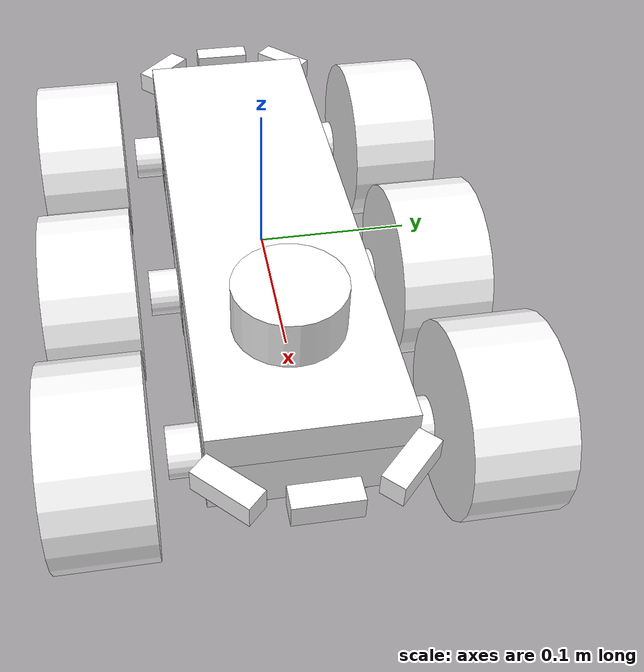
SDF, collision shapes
<sdf version='1.9'>
  <model name='wildthumper'>
    <static>0</static>
    <self_collide>0</self_collide>

    <link name='base_link'>
      <inertial>
        <pose>0 0 0 0 0 0</pose>
        <mass>0.01</mass>
        <inertia>
          <ixx>0.01</ixx>
          <ixy>0</ixy>
          <ixz>0</ixz>
          <iyy>0.01</iyy>
          <iyz>0</iyz>
          <izz>0.01</izz>
        </inertia>
      </inertial>
      <collision name='base_link_collision'>
        <pose>0 0 0 0 0 0</pose>
        <geometry>
          <box>
            <size>0.001 0.001 0.001</size>
          </box>
        </geometry>
      </collision>
      <visual name='base_link_visual'>
        <pose>0 0 0 0 0 0</pose>
        <geometry>
          <box>
            <size>0.001 0.001 0.001</size>
          </box>
        </geometry>
        <material>
          <script>
            <name>Gazebo/Orange</name>
            <uri>file://media/materials/scripts/gazebo.material</uri>
          </script>
          <diffuse>1 0.3125 0 1</diffuse>
          <ambient>1 0.3125 0 1</ambient>
        </material>
      </visual>
    </link>
    <joint name='front_small_chassis_joint' type='fixed'>
      <pose relative_to='base_link'>0.075 0 -0.02 0 0 0</pose>
      <parent>base_link</parent>
      <child>front_small_chassis_link</child>
      <axis>
        <dynamics>
          <damping>1.0</damping>
        </dynamics>
        <xyz>0 0 1</xyz>
        <limit>
          <lower>-1e16</lower>
          <upper>1e16</upper>
        </limit>
      </axis>
    </joint>
    <link name='front_small_chassis_link'>
      <pose relative_to='front_small_chassis_joint'>0 0 0 0 0 0</pose>
      <inertial>
        <pose>0 0 0 0 0 0</pose>
        <mass>0.2</mass>
        <inertia>
          <ixx>0.0002666666666666667</ixx>
          <ixy>0</ixy>
          <ixz>0</ixz>
          <iyy>0.0001083333333333333</iyy>
          <iyz>0</iyz>
          <izz>0.0003216666666666667</izz>
        </inertia>
      </inertial>
      <collision name='front_small_chassis_link_collision'>
        <pose>0 0 0 0 0 0</pose>
        <geometry>
          <box>
            <size>0.07000000000000001 0.12 0.04</size>
          </box>
        </geometry>
      </collision>
      <visual name='front_small_chassis_link_visual'>
        <pose>0 0 0 0 0 0</pose>
        <geometry>
          <mesh>
            <scale>1 1 1</scale>
            <uri>model://wildthumper/meshes/bases/small_chassis_with_frame_connector.dae</uri>
          </mesh>
        </geometry>
        <material>
          <ambient>1 1 1</ambient>
          <diffuse>1 1 1</diffuse>
          <specular>1 1 1</specular>
          <pbr>
            <metal>
              <albedo_map>model://wildthumper/materials/textures/black_metal/black_metal_diffuse.jpg</albedo_map>
              <metalness_map>model://wildthumper/materials/textures/black_metal/black_metal_metallic.jpg</metalness_map>
              <normal_map>model://wildthumper/materials/textures/black_metal/black_metal_normal.jpg</normal_map>
              <roughness_map>model://wildthumper/materials/textures/black_metal/black_metal_roughness.jpg</roughness_map>
              <roughness>1.0</roughness>
              <metalness>1.0</metalness>
            </metal>
          </pbr>
        </material>
      </visual>
    </link>
    <joint name='front_wheel_chassis_short_joint' type='fixed'>
      <pose relative_to='base_link'>0.15 0 -0.02 0 0 0</pose>
      <parent>base_link</parent>
      <child>front_wheel_chassis_short_link</child>
      <axis>
        <dynamics>
          <damping>1.0</damping>
        </dynamics>
        <xyz>0 0 1</xyz>
        <limit>
          <lower>-1e16</lower>
          <upper>1e16</upper>
        </limit>
      </axis>
    </joint>
    <link name='front_wheel_chassis_short_link'>
      <pose relative_to='front_wheel_chassis_short_joint'>0 0 0 0 0 0</pose>
      <inertial>
        <pose>0 0 0 0 0 0</pose>
        <mass>0.2</mass>
        <inertia>
          <ixx>0.0002666666666666667</ixx>
          <ixy>0</ixy>
          <ixz>0</ixz>
          <iyy>0.0001083333333333333</iyy>
          <iyz>0</iyz>
          <izz>0.0003216666666666667</izz>
        </inertia>
      </inertial>
      <collision name='front_wheel_chassis_short_link_collision'>
        <pose>0 0 0 0 0 0</pose>
        <geometry>
          <box>
            <size>0.07000000000000001 0.12 0.04</size>
          </box>
        </geometry>
      </collision>
      <visual name='front_wheel_chassis_short_link_visual'>
        <pose>0 0 0 0 0 0</pose>
        <geometry>
          <mesh>
            <scale>1 1 1</scale>
            <uri>model://wildthumper/meshes/bases/wheel_chassis_short.dae</uri>
          </mesh>
        </geometry>
        <material>
          <ambient>1 1 1</ambient>
          <diffuse>1 1 1</diffuse>
          <specular>1 1 1</specular>
          <pbr>
            <metal>
              <albedo_map>model://wildthumper/materials/textures/black_metal/black_metal_diffuse.jpg</albedo_map>
              <metalness_map>model://wildthumper/materials/textures/black_metal/black_metal_metallic.jpg</metalness_map>
              <normal_map>model://wildthumper/materials/textures/black_metal/black_metal_normal.jpg</normal_map>
              <roughness_map>model://wildthumper/materials/textures/black_metal/black_metal_roughness.jpg</roughness_map>
              <roughness>1.0</roughness>
              <metalness>1.0</metalness>
            </metal>
          </pbr>
        </material>
      </visual>
    </link>
    <joint name='front_left_motor_asm_joint' type='revolute'>
      <pose relative_to='front_wheel_chassis_short_link'>0 0.03 -0.01 0 0 0</pose>
      <parent>front_wheel_chassis_short_link</parent>
      <child>front_left_motor_asm_link</child>
      <axis>
        <xyz>1 0 0</xyz>
        <limit>
          <lower>-0.5</lower>
          <upper>0.5</upper>
          <effort>50</effort>
          <velocity>10</velocity>
        </limit>
        <dynamics>
          <damping>0.7</damping>
          <friction>0</friction>
          <spring_reference>0</spring_reference>
          <spring_stiffness>3</spring_stiffness>
        </dynamics>
      </axis>
      <physics>
        <provide_feedback>true</provide_feedback>
        <ode>
          <implicit_spring_damper>true</implicit_spring_damper>
          <cfm_damping>true</cfm_damping>
          <limit>
            <cfm>0.0</cfm>
            <erp>0.2</erp>
          </limit>
          <provide_feedback>true</provide_feedback>
        </ode>
      </physics>
    </joint>
    <link name='front_left_motor_asm_link'>
      <pose relative_to='front_left_motor_asm_joint'>0 0 0 0 0 0</pose>
      <inertial>
        <pose degrees="true">0 0.025 0 90 0 0</pose>
        <mass>0.1</mass>
        <inertia>
          <ixx>2.723333333333334e-05</ixx>
          <ixy>0</ixy>
          <ixz>0</ixz>
          <iyy>2.723333333333334e-05</iyy>
          <iyz>0</iyz>
          <izz>1.28e-05</izz>
        </inertia>
      </inertial>
      <collision name='front_left_motor_asm_link_collision'>
        <pose degrees="true">0 0 0 0 90 0</pose>
        <geometry>
          <cylinder>
            <length>0.064</length>
            <radius>0.016</radius>
          </cylinder>
        </geometry>
      </collision>
      <collision name='front_left_motor_asm_link_collision_1'>
        <pose degrees="true">0 0.025 0 90 0 0</pose>
        <geometry>
          <cylinder>
            <length>0.05</length>
            <radius>0.016</radius>
          </cylinder>
        </geometry>
      </collision>
      <visual name='front_left_motor_asm_link_visual'>
        <pose>0 0 0 0 0 0</pose>
        <geometry>
          <mesh>
            <scale>1 1 1</scale>
            <uri>model://wildthumper/meshes/bases/left_motor_asm.dae</uri>
          </mesh>
        </geometry>
        <material>
          <ambient>1 1 1</ambient>
          <diffuse>1 1 1</diffuse>
          <specular>1 1 1</specular>
          <pbr>
            <metal>
              <albedo_map>model://wildthumper/materials/textures/black_metal/black_metal_diffuse.jpg</albedo_map>
              <metalness_map>model://wildthumper/materials/textures/black_metal/black_metal_metallic.jpg</metalness_map>
              <normal_map>model://wildthumper/materials/textures/black_metal/black_metal_normal.jpg</normal_map>
              <roughness_map>model://wildthumper/materials/textures/black_metal/black_metal_roughness.jpg</roughness_map>
              <roughness>1.0</roughness>
              <metalness>1.0</metalness>
            </metal>
          </pbr>
        </material>
      </visual>
    </link>
    <joint name='front_left_wheel_joint' type='revolute'>
      <pose relative_to='front_left_motor_asm_link'>0 0.09 0 0 0 0</pose>
      <parent>front_left_motor_asm_link</parent>
      <child>front_left_wheel_link</child>
      <axis>
        <xyz>0 1 0</xyz>
        <limit>
          <lower>-1e16</lower>
          <upper>1e16</upper>
        </limit>
        <dynamics>
          <damping>0.02</damping>
        </dynamics>
      </axis>
    </joint>
    <link name='front_left_wheel_link'>
      <pose relative_to='front_left_wheel_joint'>0 0 0 0 0 0</pose>
      <inertial>
        <pose degrees="true">0 0 0 90 0 0</pose>
        <mass>0.19</mass>
        <inertia>
          <ixx>0.0002022409166666667</ixx>
          <ixy>0</ixy>
          <ixz>0</ixz>
          <iyy>0.0002022409166666667</iyy>
          <iyz>1.203706215242022e-35</iyz>
          <izz>0.0002973904999999999</izz>
        </inertia>
      </inertial>
      <collision name='front_left_wheel_link_collision'>
        <pose degrees="true">0 0 0 90 0 0</pose>
        <geometry>
          <cylinder>
            <length>0.062</length>
            <radius>0.062</radius>
          </cylinder>
        </geometry>
        <surface>
          <friction>
            <ode>
              <mu>10.0</mu>
              <mu2>10.0</mu2>
              <fdir1>1 0 0</fdir1>
              <slip1>0.0</slip1>
              <slip2>0.0</slip2>
            </ode>
          </friction>
        </surface>
      </collision>
      <collision name='front_left_wheel_link_fixed_joint_lump__front_left_wheel_adapter_link_collision_1'>
        <pose degrees="true">0 0 0 90 0 0</pose>
        <geometry>
          <cylinder>
            <length>0.024</length>
            <radius>0.005</radius>
          </cylinder>
        </geometry>
      </collision>
      <collision name='front_left_wheel_link_fixed_joint_lump__front_left_wheel_rim_link_collision_2'>
        <pose degrees="true">0 0 0 90 0 0</pose>
        <geometry>
          <cylinder>
            <length>0.05</length>
            <radius>0.03</radius>
          </cylinder>
        </geometry>
      </collision>
      <visual name='front_left_wheel_link_visual'>
        <pose>0 0 0 0 0 0</pose>
        <geometry>
          <mesh>
            <scale>1 1 1</scale>
            <uri>model://wildthumper/meshes/wheels/left_wheel_tyre.dae</uri>
          </mesh>
        </geometry>
        <material>
          <ambient>1 1 1</ambient>
          <diffuse>1 1 1</diffuse>
          <specular>1 1 1</specular>
          <pbr>
            <metal>
              <albedo_map>model://wildthumper/materials/textures/rubber_01/rubber_01_diffuse.jpg</albedo_map>
              <normal_map>model://wildthumper/materials/textures/rubber_01/rubber_01_normal.jpg</normal_map>
              <roughness_map>model://wildthumper/materials/textures/rubber_01/rubber_01_roughness.jpg</roughness_map>
              <roughness>1.0</roughness>
              <metalness>0.0</metalness>
            </metal>
          </pbr>
        </material>
      </visual>
      <visual name='front_left_wheel_link_fixed_joint_lump__front_left_wheel_adapter_link_visual_1'>
        <pose>0 0 0 0 0 0</pose>
        <geometry>
          <mesh>
            <scale>1 1 1</scale>
            <uri>model://wildthumper/meshes/wheels/left_wheel_adapter.dae</uri>
          </mesh>
        </geometry>
        <material>
          <ambient>1 1 1</ambient>
          <diffuse>1 1 1</diffuse>
          <specular>1 1 1</specular>
          <pbr>
            <metal>
              <albedo_map>model://wildthumper/materials/textures/silver_metal/silver_metal_diffuse.jpg</albedo_map>
              <metalness_map>model://wildthumper/materials/textures/silver_metal/silver_metal_metallic.jpg</metalness_map>
              <normal_map>model://wildthumper/materials/textures/silver_metal/silver_metal_normal.jpg</normal_map>
              <roughness_map>model://wildthumper/materials/textures/silver_metal/silver_metal_roughness.jpg</roughness_map>
              <roughness>1.0</roughness>
              <metalness>1.0</metalness>
            </metal>
          </pbr>
        </material>
      </visual>
      <visual name='front_left_wheel_link_fixed_joint_lump__front_left_wheel_rim_link_visual_2'>
        <pose>0 0 0 0 0 0</pose>
        <geometry>
          <mesh>
            <scale>1 1 1</scale>
            <uri>model://wildthumper/meshes/wheels/left_wheel_rim.dae</uri>
          </mesh>
        </geometry>
        <material>
          <ambient>1 1 1</ambient>
          <diffuse>1 1 1</diffuse>
          <specular>1 1 1</specular>
          <pbr>
            <metal>
              <albedo_map>model://wildthumper/materials/textures/red_metal/red_metal_diffuse.jpg</albedo_map>
              <metalness_map>model://wildthumper/materials/textures/red_metal/red_metal_metallic.jpg</metalness_map>
              <normal_map>model://wildthumper/materials/textures/red_metal/red_metal_normal.jpg</normal_map>
              <roughness_map>model://wildthumper/materials/textures/red_metal/red_metal_roughness.jpg</roughness_map>
              <roughness>1.0</roughness>
              <metalness>1.0</metalness>
            </metal>
          </pbr>
        </material>
      </visual>
    </link>
    <joint name='front_right_motor_asm_joint' type='revolute'>
      <pose relative_to='front_wheel_chassis_short_link'>0 -0.03 -0.01 0 0 0</pose>
      <parent>front_wheel_chassis_short_link</parent>
      <child>front_right_motor_asm_link</child>
      <axis>
        <xyz>1 0 0</xyz>
        <limit>
          <lower>-0.5</lower>
          <upper>0.5</upper>
          <effort>50</effort>
          <velocity>10</velocity>
        </limit>
        <dynamics>
          <damping>0.7</damping>
          <friction>0</friction>
          <spring_reference>0</spring_reference>
          <spring_stiffness>3</spring_stiffness>
        </dynamics>
      </axis>
    </joint>
    <link name='front_right_motor_asm_link'>
      <pose relative_to='front_right_motor_asm_joint'>0 0 0 0 0 0</pose>
      <inertial>
        <pose degrees="true">0 -0.025 0 90 0 0</pose>
        <mass>0.1</mass>
        <inertia>
          <ixx>2.723333333333334e-05</ixx>
          <ixy>0</ixy>
          <ixz>0</ixz>
          <iyy>2.723333333333334e-05</iyy>
          <iyz>0</iyz>
          <izz>1.28e-05</izz>
        </inertia>
      </inertial>
      <collision name='front_right_motor_asm_link_collision'>
        <pose degrees="true">0 0 0 0 90 0</pose>
        <geometry>
          <cylinder>
            <length>0.064</length>
            <radius>0.016</radius>
          </cylinder>
        </geometry>
      </collision>
      <collision name='front_right_motor_asm_link_collision_1'>
        <pose degrees="true">0 -0.025 0 90 0 0</pose>
        <geometry>
          <cylinder>
            <length>0.05</length>
            <radius>0.016</radius>
          </cylinder>
        </geometry>
      </collision>
      <visual name='front_right_motor_asm_link_visual'>
        <pose>0 0 0 0 0 0</pose>
        <geometry>
          <mesh>
            <scale>1 1 1</scale>
            <uri>model://wildthumper/meshes/bases/right_motor_asm.dae</uri>
          </mesh>
        </geometry>
        <material>
          <ambient>1 1 1</ambient>
          <diffuse>1 1 1</diffuse>
          <specular>1 1 1</specular>
          <pbr>
            <metal>
              <albedo_map>model://wildthumper/materials/textures/black_metal/black_metal_diffuse.jpg</albedo_map>
              <metalness_map>model://wildthumper/materials/textures/black_metal/black_metal_metallic.jpg</metalness_map>
              <normal_map>model://wildthumper/materials/textures/black_metal/black_metal_normal.jpg</normal_map>
              <roughness_map>model://wildthumper/materials/textures/black_metal/black_metal_roughness.jpg</roughness_map>
              <roughness>1.0</roughness>
              <metalness>1.0</metalness>
            </metal>
          </pbr>
        </material>
      </visual>
    </link>
    <joint name='front_right_wheel_joint' type='revolute'>
      <pose relative_to='front_right_motor_asm_link'>0 -0.09 0 0 0 0</pose>
      <parent>front_right_motor_asm_link</parent>
      <child>front_right_wheel_link</child>
      <axis>
        <xyz>0 1 0</xyz>
        <limit>
          <lower>-1e16</lower>
          <upper>1e16</upper>
        </limit>
        <dynamics>
          <damping>0.02</damping>
        </dynamics>
      </axis>
    </joint>
    <link name='front_right_wheel_link'>
      <pose relative_to='front_right_wheel_joint'>0 0 0 0 0 0</pose>
      <inertial>
        <pose degrees="true">0 0 0 90 0 0</pose>
        <mass>0.19</mass>
        <inertia>
          <ixx>0.0002022409166666667</ixx>
          <ixy>0</ixy>
          <ixz>0</ixz>
          <iyy>0.0002022409166666667</iyy>
          <iyz>1.203706215242022e-35</iyz>
          <izz>0.0002973904999999999</izz>
        </inertia>
      </inertial>
      <collision name='front_right_wheel_link_collision'>
        <pose degrees="true">0 0 0 90 0 0</pose>
        <geometry>
          <cylinder>
            <length>0.062</length>
            <radius>0.062</radius>
          </cylinder>
        </geometry>
        <surface>
          <friction>
            <ode>
              <mu>10.0</mu>
              <mu2>10.0</mu2>
              <fdir1>1 0 0</fdir1>
              <slip1>0.0</slip1>
              <slip2>0.0</slip2>
            </ode>
          </friction>
        </surface>
      </collision>
      <collision name='front_right_wheel_link_fixed_joint_lump__front_right_wheel_adapter_link_collision_1'>
        <pose degrees="true">0 0 0 90 0 0</pose>
        <geometry>
          <cylinder>
            <length>0.024</length>
            <radius>0.005</radius>
          </cylinder>
        </geometry>
      </collision>
      <collision name='front_right_wheel_link_fixed_joint_lump__front_right_wheel_rim_link_collision_2'>
        <pose degrees="true">0 0 0 90 0 0</pose>
        <geometry>
          <cylinder>
            <length>0.05</length>
            <radius>0.03</radius>
          </cylinder>
        </geometry>
      </collision>
      <visual name='front_right_wheel_link_visual'>
        <pose>0 0 0 0 0 0</pose>
        <geometry>
          <mesh>
            <scale>1 1 1</scale>
            <uri>model://wildthumper/meshes/wheels/right_wheel_tyre.dae</uri>
          </mesh>
        </geometry>
        <material>
          <ambient>1 1 1</ambient>
          <diffuse>1 1 1</diffuse>
          <specular>1 1 1</specular>
          <pbr>
            <metal>
              <albedo_map>model://wildthumper/materials/textures/rubber_01/rubber_01_diffuse.jpg</albedo_map>
              <normal_map>model://wildthumper/materials/textures/rubber_01/rubber_01_normal.jpg</normal_map>
              <roughness_map>model://wildthumper/materials/textures/rubber_01/rubber_01_roughness.jpg</roughness_map>
              <roughness>1.0</roughness>
              <metalness>0.0</metalness>
            </metal>
          </pbr>
        </material>
      </visual>
      <visual name='front_right_wheel_link_fixed_joint_lump__front_right_wheel_adapter_link_visual_1'>
        <pose>0 0 0 0 0 0</pose>
        <geometry>
          <mesh>
            <scale>1 1 1</scale>
            <uri>model://wildthumper/meshes/wheels/right_wheel_adapter.dae</uri>
          </mesh>
        </geometry>
        <material>
          <ambient>1 1 1</ambient>
          <diffuse>1 1 1</diffuse>
          <specular>1 1 1</specular>
          <pbr>
            <metal>
              <albedo_map>model://wildthumper/materials/textures/silver_metal/silver_metal_diffuse.jpg</albedo_map>
              <metalness_map>model://wildthumper/materials/textures/silver_metal/silver_metal_metallic.jpg</metalness_map>
              <normal_map>model://wildthumper/materials/textures/silver_metal/silver_metal_normal.jpg</normal_map>
              <roughness_map>model://wildthumper/materials/textures/silver_metal/silver_metal_roughness.jpg</roughness_map>
              <roughness>1.0</roughness>
              <metalness>1.0</metalness>
            </metal>
          </pbr>
        </material>
      </visual>
      <visual name='front_right_wheel_link_fixed_joint_lump__front_right_wheel_rim_link_visual_2'>
        <pose>0 0 0 0 0 0</pose>
        <geometry>
          <mesh>
            <scale>1 1 1</scale>
            <uri>model://wildthumper/meshes/wheels/right_wheel_rim.dae</uri>
          </mesh>
        </geometry>
        <material>
          <ambient>1 1 1</ambient>
          <diffuse>1 1 1</diffuse>
          <specular>1 1 1</specular>
          <pbr>
            <metal>
              <albedo_map>model://wildthumper/materials/textures/red_metal/red_metal_diffuse.jpg</albedo_map>
              <metalness_map>model://wildthumper/materials/textures/red_metal/red_metal_metallic.jpg</metalness_map>
              <normal_map>model://wildthumper/materials/textures/red_metal/red_metal_normal.jpg</normal_map>
              <roughness_map>model://wildthumper/materials/textures/red_metal/red_metal_roughness.jpg</roughness_map>
              <roughness>1.0</roughness>
              <metalness>1.0</metalness>
            </metal>
          </pbr>
        </material>
      </visual>
    </link>
    <joint name='mid_wheel_chassis_long_joint' type='fixed'>
      <pose relative_to='base_link'>0 0 -0.025 0 0 0</pose>
      <parent>base_link</parent>
      <child>mid_wheel_chassis_long_link</child>
      <axis>
        <dynamics>
          <damping>1.0</damping>
        </dynamics>
        <xyz>0 0 1</xyz>
        <limit>
          <lower>-1e16</lower>
          <upper>1e16</upper>
        </limit>
      </axis>
    </joint>
    <link name='mid_wheel_chassis_long_link'>
      <pose relative_to='mid_wheel_chassis_long_joint'>0 0 0 0 0 0</pose>
      <inertial>
        <pose>0 0 0 0 0 0</pose>
        <mass>0.2</mass>
        <inertia>
          <ixx>0.0002816666666666667</ixx>
          <ixy>0</ixy>
          <ixz>0</ixz>
          <iyy>0.0001233333333333334</iyy>
          <iyz>0</iyz>
          <izz>0.0003216666666666667</izz>
        </inertia>
      </inertial>
      <collision name='mid_wheel_chassis_long_link_collision'>
        <pose>0 0 0 0 0 0</pose>
        <geometry>
          <box>
            <size>0.07000000000000001 0.12 0.05</size>
          </box>
        </geometry>
      </collision>
      <visual name='mid_wheel_chassis_long_link_visual'>
        <pose>0 0 0.005 0 0 0</pose>
        <geometry>
          <mesh>
            <scale>1 1 1</scale>
            <uri>model://wildthumper/meshes/bases/wheel_chassis_long.dae</uri>
          </mesh>
        </geometry>
        <material>
          <ambient>1 1 1</ambient>
          <diffuse>1 1 1</diffuse>
          <specular>1 1 1</specular>
          <pbr>
            <metal>
              <albedo_map>model://wildthumper/materials/textures/black_metal/black_metal_diffuse.jpg</albedo_map>
              <metalness_map>model://wildthumper/materials/textures/black_metal/black_metal_metallic.jpg</metalness_map>
              <normal_map>model://wildthumper/materials/textures/black_metal/black_metal_normal.jpg</normal_map>
              <roughness_map>model://wildthumper/materials/textures/black_metal/black_metal_roughness.jpg</roughness_map>
              <roughness>1.0</roughness>
              <metalness>1.0</metalness>
            </metal>
          </pbr>
        </material>
      </visual>
    </link>
    <joint name='mid_left_motor_asm_joint' type='revolute'>
      <pose relative_to='mid_wheel_chassis_long_link'>0 0.03 -0.015 0 0 0</pose>
      <parent>mid_wheel_chassis_long_link</parent>
      <child>mid_left_motor_asm_link</child>
      <axis>
        <xyz>1 0 0</xyz>
        <limit>
          <lower>-0.5</lower>
          <upper>0.5</upper>
          <effort>50</effort>
          <velocity>10</velocity>
        </limit>
        <dynamics>
          <damping>0.7</damping>
          <friction>0</friction>
          <spring_reference>0</spring_reference>
          <spring_stiffness>3</spring_stiffness>
        </dynamics>
      </axis>
    </joint>
    <link name='mid_left_motor_asm_link'>
      <pose relative_to='mid_left_motor_asm_joint'>0 0 0 0 0 0</pose>
      <inertial>
        <pose degrees="true">0 0.025 0 90 0 0</pose>
        <mass>0.1</mass>
        <inertia>
          <ixx>2.723333333333334e-05</ixx>
          <ixy>0</ixy>
          <ixz>0</ixz>
          <iyy>2.723333333333334e-05</iyy>
          <iyz>0</iyz>
          <izz>1.28e-05</izz>
        </inertia>
      </inertial>
      <collision name='mid_left_motor_asm_link_collision'>
        <pose degrees="true">0 0 0 0 90 0</pose>
        <geometry>
          <cylinder>
            <length>0.064</length>
            <radius>0.016</radius>
          </cylinder>
        </geometry>
      </collision>
      <collision name='mid_left_motor_asm_link_collision_1'>
        <pose degrees="true">0 0.025 0 90 0 0</pose>
        <geometry>
          <cylinder>
            <length>0.05</length>
            <radius>0.016</radius>
          </cylinder>
        </geometry>
      </collision>
      <visual name='mid_left_motor_asm_link_visual'>
        <pose>0 0 0 0 0 0</pose>
        <geometry>
          <mesh>
            <scale>1 1 1</scale>
            <uri>model://wildthumper/meshes/bases/left_motor_asm.dae</uri>
          </mesh>
        </geometry>
        <material>
          <ambient>1 1 1</ambient>
          <diffuse>1 1 1</diffuse>
          <specular>1 1 1</specular>
          <pbr>
            <metal>
              <albedo_map>model://wildthumper/materials/textures/black_metal/black_metal_diffuse.jpg</albedo_map>
              <metalness_map>model://wildthumper/materials/textures/black_metal/black_metal_metallic.jpg</metalness_map>
              <normal_map>model://wildthumper/materials/textures/black_metal/black_metal_normal.jpg</normal_map>
              <roughness_map>model://wildthumper/materials/textures/black_metal/black_metal_roughness.jpg</roughness_map>
              <roughness>1.0</roughness>
              <metalness>1.0</metalness>
            </metal>
          </pbr>
        </material>
      </visual>
    </link>
    <joint name='mid_left_wheel_joint' type='revolute'>
      <pose relative_to='mid_left_motor_asm_link'>0 0.09 0 0 0 0</pose>
      <parent>mid_left_motor_asm_link</parent>
      <child>mid_left_wheel_link</child>
      <axis>
        <xyz>0 1 0</xyz>
        <limit>
          <lower>-1e16</lower>
          <upper>1e16</upper>
        </limit>
        <dynamics>
          <damping>0.02</damping>
        </dynamics>
      </axis>
    </joint>
    <link name='mid_left_wheel_link'>
      <pose relative_to='mid_left_wheel_joint'>0 0 0 0 0 0</pose>
      <inertial>
        <pose degrees="true">0 0 0 90 0 0</pose>
        <mass>0.19</mass>
        <inertia>
          <ixx>0.0002022409166666667</ixx>
          <ixy>0</ixy>
          <ixz>0</ixz>
          <iyy>0.0002022409166666667</iyy>
          <iyz>1.203706215242022e-35</iyz>
          <izz>0.0002973904999999999</izz>
        </inertia>
      </inertial>
      <collision name='mid_left_wheel_link_collision'>
        <pose degrees="true">0 0 0 90 0 0</pose>
        <geometry>
          <cylinder>
            <length>0.062</length>
            <radius>0.062</radius>
          </cylinder>
        </geometry>
        <surface>
          <friction>
            <ode>
              <mu>10.0</mu>
              <mu2>10.0</mu2>
              <fdir1>1 0 0</fdir1>
              <slip1>0.0</slip1>
              <slip2>0.0</slip2>
            </ode>
          </friction>
        </surface>
      </collision>
      <collision name='mid_left_wheel_link_fixed_joint_lump__mid_left_wheel_adapter_link_collision_1'>
        <pose degrees="true">0 0 0 90 0 0</pose>
        <geometry>
          <cylinder>
            <length>0.024</length>
            <radius>0.005</radius>
          </cylinder>
        </geometry>
      </collision>
      <collision name='mid_left_wheel_link_fixed_joint_lump__mid_left_wheel_rim_link_collision_2'>
        <pose degrees="true">0 0 0 90 0 0</pose>
        <geometry>
          <cylinder>
            <length>0.05</length>
            <radius>0.03</radius>
          </cylinder>
        </geometry>
      </collision>
      <visual name='mid_left_wheel_link_visual'>
        <pose>0 0 0 0 0 0</pose>
        <geometry>
          <mesh>
            <scale>1 1 1</scale>
            <uri>model://wildthumper/meshes/wheels/left_wheel_tyre.dae</uri>
          </mesh>
        </geometry>
        <material>
          <ambient>1 1 1</ambient>
          <diffuse>1 1 1</diffuse>
          <specular>1 1 1</specular>
          <pbr>
            <metal>
              <albedo_map>model://wildthumper/materials/textures/rubber_01/rubber_01_diffuse.jpg</albedo_map>
              <normal_map>model://wildthumper/materials/textures/rubber_01/rubber_01_normal.jpg</normal_map>
              <roughness_map>model://wildthumper/materials/textures/rubber_01/rubber_01_roughness.jpg</roughness_map>
              <roughness>1.0</roughness>
              <metalness>0.0</metalness>
            </metal>
          </pbr>
        </material>
      </visual>
      <visual name='mid_left_wheel_link_fixed_joint_lump__mid_left_wheel_adapter_link_visual_1'>
        <pose>0 0 0 0 0 0</pose>
        <geometry>
          <mesh>
            <scale>1 1 1</scale>
            <uri>model://wildthumper/meshes/wheels/left_wheel_adapter.dae</uri>
          </mesh>
        </geometry>
        <material>
          <ambient>1 1 1</ambient>
          <diffuse>1 1 1</diffuse>
          <specular>1 1 1</specular>
          <pbr>
            <metal>
              <albedo_map>model://wildthumper/materials/textures/silver_metal/silver_metal_diffuse.jpg</albedo_map>
              <metalness_map>model://wildthumper/materials/textures/silver_metal/silver_metal_metallic.jpg</metalness_map>
              <normal_map>model://wildthumper/materials/textures/silver_metal/silver_metal_normal.jpg</normal_map>
              <roughness_map>model://wildthumper/materials/textures/silver_metal/silver_metal_roughness.jpg</roughness_map>
              <roughness>1.0</roughness>
              <metalness>1.0</metalness>
            </metal>
          </pbr>
        </material>
      </visual>
      <visual name='mid_left_wheel_link_fixed_joint_lump__mid_left_wheel_rim_link_visual_2'>
        <pose>0 0 0 0 0 0</pose>
        <geometry>
          <mesh>
            <scale>1 1 1</scale>
            <uri>model://wildthumper/meshes/wheels/left_wheel_rim.dae</uri>
          </mesh>
        </geometry>
        <material>
          <ambient>1 1 1</ambient>
          <diffuse>1 1 1</diffuse>
          <specular>1 1 1</specular>
          <pbr>
            <metal>
              <albedo_map>model://wildthumper/materials/textures/red_metal/red_metal_diffuse.jpg</albedo_map>
              <metalness_map>model://wildthumper/materials/textures/red_metal/red_metal_metallic.jpg</metalness_map>
              <normal_map>model://wildthumper/materials/textures/red_metal/red_metal_normal.jpg</normal_map>
              <roughness_map>model://wildthumper/materials/textures/red_metal/red_metal_roughness.jpg</roughness_map>
              <roughness>1.0</roughness>
              <metalness>1.0</metalness>
            </metal>
          </pbr>
        </material>
      </visual>
    </link>
    <joint name='mid_right_motor_asm_joint' type='revolute'>
      <pose relative_to='mid_wheel_chassis_long_link'>0 -0.03 -0.015 0 0 0</pose>
      <parent>mid_wheel_chassis_long_link</parent>
      <child>mid_right_motor_asm_link</child>
      <axis>
        <xyz>1 0 0</xyz>
        <limit>
          <lower>-0.5</lower>
          <upper>0.5</upper>
          <effort>50</effort>
          <velocity>10</velocity>
        </limit>
        <dynamics>
          <damping>0.7</damping>
          <friction>0</friction>
          <spring_reference>0</spring_reference>
          <spring_stiffness>3</spring_stiffness>
        </dynamics>
      </axis>
    </joint>
    <link name='mid_right_motor_asm_link'>
      <pose relative_to='mid_right_motor_asm_joint'>0 0 0 0 0 0</pose>
      <inertial>
        <pose degrees="true">0 -0.025 0 90 0 0</pose>
        <mass>0.1</mass>
        <inertia>
          <ixx>2.723333333333334e-05</ixx>
          <ixy>0</ixy>
          <ixz>0</ixz>
          <iyy>2.723333333333334e-05</iyy>
          <iyz>0</iyz>
          <izz>1.28e-05</izz>
        </inertia>
      </inertial>
      <collision name='mid_right_motor_asm_link_collision'>
        <pose degrees="true">0 0 0 0 90 0</pose>
        <geometry>
          <cylinder>
            <length>0.064</length>
            <radius>0.016</radius>
          </cylinder>
        </geometry>
      </collision>
      <collision name='mid_right_motor_asm_link_collision_1'>
        <pose degrees="true">0 -0.025 0 90 0 0</pose>
        <geometry>
          <cylinder>
            <length>0.05</length>
            <radius>0.016</radius>
          </cylinder>
        </geometry>
      </collision>
      <visual name='mid_right_motor_asm_link_visual'>
        <pose>0 0 0 0 0 0</pose>
        <geometry>
          <mesh>
            <scale>1 1 1</scale>
            <uri>model://wildthumper/meshes/bases/right_motor_asm.dae</uri>
          </mesh>
        </geometry>
        <material>
          <ambient>1 1 1</ambient>
          <diffuse>1 1 1</diffuse>
          <specular>1 1 1</specular>
          <pbr>
            <metal>
              <albedo_map>model://wildthumper/materials/textures/black_metal/black_metal_diffuse.jpg</albedo_map>
              <metalness_map>model://wildthumper/materials/textures/black_metal/black_metal_metallic.jpg</metalness_map>
              <normal_map>model://wildthumper/materials/textures/black_metal/black_metal_normal.jpg</normal_map>
              <roughness_map>model://wildthumper/materials/textures/black_metal/black_metal_roughness.jpg</roughness_map>
              <roughness>1.0</roughness>
              <metalness>1.0</metalness>
            </metal>
          </pbr>
        </material>
      </visual>
    </link>
    <joint name='mid_right_wheel_joint' type='revolute'>
      <pose relative_to='mid_right_motor_asm_link'>0 -0.09 0 0 0 0</pose>
      <parent>mid_right_motor_asm_link</parent>
      <child>mid_right_wheel_link</child>
      <axis>
        <xyz>0 1 0</xyz>
        <limit>
          <lower>-1e16</lower>
          <upper>1e16</upper>
        </limit>
        <dynamics>
          <damping>0.02</damping>
        </dynamics>
      </axis>
    </joint>
    <link name='mid_right_wheel_link'>
      <pose relative_to='mid_right_wheel_joint'>0 0 0 0 0 0</pose>
      <inertial>
        <pose degrees="true">0 0 0 90 0 0</pose>
        <mass>0.19</mass>
        <inertia>
          <ixx>0.0002022409166666667</ixx>
          <ixy>0</ixy>
          <ixz>0</ixz>
          <iyy>0.0002022409166666667</iyy>
          <iyz>1.203706215242022e-35</iyz>
          <izz>0.0002973904999999999</izz>
        </inertia>
      </inertial>
      <collision name='mid_right_wheel_link_collision'>
        <pose degrees="true">0 0 0 90 0 0</pose>
        <geometry>
          <cylinder>
            <length>0.062</length>
            <radius>0.062</radius>
          </cylinder>
        </geometry>
        <surface>
          <friction>
            <ode>
              <mu>10.0</mu>
              <mu2>10.0</mu2>
              <fdir1>1 0 0</fdir1>
              <slip1>0.0</slip1>
              <slip2>0.0</slip2>
            </ode>
          </friction>
        </surface>
      </collision>
      <collision name='mid_right_wheel_link_fixed_joint_lump__mid_right_wheel_adapter_link_collision_1'>
        <pose degrees="true">0 0 0 90 0 0</pose>
        <geometry>
          <cylinder>
            <length>0.024</length>
            <radius>0.005</radius>
          </cylinder>
        </geometry>
      </collision>
      <collision name='mid_right_wheel_link_fixed_joint_lump__mid_right_wheel_rim_link_collision_2'>
        <pose degrees="true">0 0 0 90 0 0</pose>
        <geometry>
          <cylinder>
            <length>0.05</length>
            <radius>0.03</radius>
          </cylinder>
        </geometry>
      </collision>
      <visual name='mid_right_wheel_link_visual'>
        <pose>0 0 0 0 0 0</pose>
        <geometry>
          <mesh>
            <scale>1 1 1</scale>
            <uri>model://wildthumper/meshes/wheels/right_wheel_tyre.dae</uri>
          </mesh>
        </geometry>
        <material>
          <ambient>1 1 1</ambient>
          <diffuse>1 1 1</diffuse>
          <specular>1 1 1</specular>
          <pbr>
            <metal>
              <albedo_map>model://wildthumper/materials/textures/rubber_01/rubber_01_diffuse.jpg</albedo_map>
              <normal_map>model://wildthumper/materials/textures/rubber_01/rubber_01_normal.jpg</normal_map>
              <roughness_map>model://wildthumper/materials/textures/rubber_01/rubber_01_roughness.jpg</roughness_map>
              <roughness>1.0</roughness>
              <metalness>0.0</metalness>
            </metal>
          </pbr>
        </material>
      </visual>
      <visual name='mid_right_wheel_link_fixed_joint_lump__mid_right_wheel_adapter_link_visual_1'>
        <pose>0 0 0 0 0 0</pose>
        <geometry>
          <mesh>
            <scale>1 1 1</scale>
            <uri>model://wildthumper/meshes/wheels/right_wheel_adapter.dae</uri>
          </mesh>
        </geometry>
        <material>
          <ambient>1 1 1</ambient>
          <diffuse>1 1 1</diffuse>
          <specular>1 1 1</specular>
          <pbr>
            <metal>
              <albedo_map>model://wildthumper/materials/textures/silver_metal/silver_metal_diffuse.jpg</albedo_map>
              <metalness_map>model://wildthumper/materials/textures/silver_metal/silver_metal_metallic.jpg</metalness_map>
              <normal_map>model://wildthumper/materials/textures/silver_metal/silver_metal_normal.jpg</normal_map>
              <roughness_map>model://wildthumper/materials/textures/silver_metal/silver_metal_roughness.jpg</roughness_map>
              <roughness>1.0</roughness>
              <metalness>1.0</metalness>
            </metal>
          </pbr>
        </material>
      </visual>
      <visual name='mid_right_wheel_link_fixed_joint_lump__mid_right_wheel_rim_link_visual_2'>
        <pose>0 0 0 0 0 0</pose>
        <geometry>
          <mesh>
            <scale>1 1 1</scale>
            <uri>model://wildthumper/meshes/wheels/right_wheel_rim.dae</uri>
          </mesh>
        </geometry>
        <material>
          <ambient>1 1 1</ambient>
          <diffuse>1 1 1</diffuse>
          <specular>1 1 1</specular>
          <pbr>
            <metal>
              <albedo_map>model://wildthumper/materials/textures/red_metal/red_metal_diffuse.jpg</albedo_map>
              <metalness_map>model://wildthumper/materials/textures/red_metal/red_metal_metallic.jpg</metalness_map>
              <normal_map>model://wildthumper/materials/textures/red_metal/red_metal_normal.jpg</normal_map>
              <roughness_map>model://wildthumper/materials/textures/red_metal/red_metal_roughness.jpg</roughness_map>
              <roughness>1.0</roughness>
              <metalness>1.0</metalness>
            </metal>
          </pbr>
        </material>
      </visual>
    </link>
    <joint name='rear_small_chassis_joint' type='fixed'>
      <pose relative_to='base_link'>-0.075 0 -0.02 0 0 0</pose>
      <parent>base_link</parent>
      <child>rear_small_chassis_link</child>
      <axis>
        <dynamics>
          <damping>1.0</damping>
        </dynamics>
        <xyz>0 0 1</xyz>
        <limit>
          <lower>-1e16</lower>
          <upper>1e16</upper>
        </limit>
      </axis>
    </joint>
    <link name='rear_small_chassis_link'>
      <pose relative_to='rear_small_chassis_joint'>0 0 0 0 0 0</pose>
      <inertial>
        <pose>0 0 0 0 0 0</pose>
        <mass>0.2</mass>
        <inertia>
          <ixx>0.0002666666666666667</ixx>
          <ixy>0</ixy>
          <ixz>0</ixz>
          <iyy>0.0001083333333333333</iyy>
          <iyz>0</iyz>
          <izz>0.0003216666666666667</izz>
        </inertia>
      </inertial>
      <collision name='rear_small_chassis_link_collision'>
        <pose>0 0 0 0 0 0</pose>
        <geometry>
          <box>
            <size>0.07000000000000001 0.12 0.04</size>
          </box>
        </geometry>
      </collision>
      <visual name='rear_small_chassis_link_visual'>
        <pose>0 0 0 0 0 0</pose>
        <geometry>
          <mesh>
            <scale>1 1 1</scale>
            <uri>model://wildthumper/meshes/bases/small_chassis_with_frame_connector.dae</uri>
          </mesh>
        </geometry>
        <material>
          <ambient>1 1 1</ambient>
          <diffuse>1 1 1</diffuse>
          <specular>1 1 1</specular>
          <pbr>
            <metal>
              <albedo_map>model://wildthumper/materials/textures/black_metal/black_metal_diffuse.jpg</albedo_map>
              <metalness_map>model://wildthumper/materials/textures/black_metal/black_metal_metallic.jpg</metalness_map>
              <normal_map>model://wildthumper/materials/textures/black_metal/black_metal_normal.jpg</normal_map>
              <roughness_map>model://wildthumper/materials/textures/black_metal/black_metal_roughness.jpg</roughness_map>
              <roughness>1.0</roughness>
              <metalness>1.0</metalness>
            </metal>
          </pbr>
        </material>
      </visual>
    </link>
    <joint name='rear_wheel_chassis_short_joint' type='fixed'>
      <pose relative_to='base_link'>-0.15 0 -0.02 0 0 0</pose>
      <parent>base_link</parent>
      <child>rear_wheel_chassis_short_link</child>
      <axis>
        <dynamics>
          <damping>1.0</damping>
        </dynamics>
        <xyz>0 0 1</xyz>
        <limit>
          <lower>-1e16</lower>
          <upper>1e16</upper>
        </limit>
      </axis>
    </joint>
    <link name='rear_wheel_chassis_short_link'>
      <pose relative_to='rear_wheel_chassis_short_joint'>0 0 0 0 0 0</pose>
      <inertial>
        <pose>0 0 0 0 0 0</pose>
        <mass>0.2</mass>
        <inertia>
          <ixx>0.0002666666666666667</ixx>
          <ixy>0</ixy>
          <ixz>0</ixz>
          <iyy>0.0001083333333333333</iyy>
          <iyz>0</iyz>
          <izz>0.0003216666666666667</izz>
        </inertia>
      </inertial>
      <collision name='rear_wheel_chassis_short_link_collision'>
        <pose>0 0 0 0 0 0</pose>
        <geometry>
          <box>
            <size>0.07000000000000001 0.12 0.04</size>
          </box>
        </geometry>
      </collision>
      <visual name='rear_wheel_chassis_short_link_visual'>
        <pose>0 0 0 0 0 0</pose>
        <geometry>
          <mesh>
            <scale>1 1 1</scale>
            <uri>model://wildthumper/meshes/bases/wheel_chassis_short.dae</uri>
          </mesh>
        </geometry>
        <material>
          <ambient>1 1 1</ambient>
          <diffuse>1 1 1</diffuse>
          <specular>1 1 1</specular>
          <pbr>
            <metal>
              <albedo_map>model://wildthumper/materials/textures/black_metal/black_metal_diffuse.jpg</albedo_map>
              <metalness_map>model://wildthumper/materials/textures/black_metal/black_metal_metallic.jpg</metalness_map>
              <normal_map>model://wildthumper/materials/textures/black_metal/black_metal_normal.jpg</normal_map>
              <roughness_map>model://wildthumper/materials/textures/black_metal/black_metal_roughness.jpg</roughness_map>
              <roughness>1.0</roughness>
              <metalness>1.0</metalness>
            </metal>
          </pbr>
        </material>
      </visual>
    </link>
    <joint name='rear_left_motor_asm_joint' type='revolute'>
      <pose relative_to='rear_wheel_chassis_short_link'>0 0.03 -0.01 0 0 0</pose>
      <parent>rear_wheel_chassis_short_link</parent>
      <child>rear_left_motor_asm_link</child>
      <axis>
        <xyz>1 0 0</xyz>
        <limit>
          <lower>-0.5</lower>
          <upper>0.5</upper>
          <effort>50</effort>
          <velocity>10</velocity>
        </limit>
        <dynamics>
          <damping>0.7</damping>
          <friction>0</friction>
          <spring_reference>0</spring_reference>
          <spring_stiffness>3</spring_stiffness>
        </dynamics>
      </axis>
    </joint>
    <link name='rear_left_motor_asm_link'>
      <pose relative_to='rear_left_motor_asm_joint'>0 0 0 0 0 0</pose>
      <inertial>
        <pose degrees="true">0 0.025 0 90 0 0</pose>
        <mass>0.1</mass>
        <inertia>
          <ixx>2.723333333333334e-05</ixx>
          <ixy>0</ixy>
          <ixz>0</ixz>
          <iyy>2.723333333333334e-05</iyy>
          <iyz>0</iyz>
          <izz>1.28e-05</izz>
        </inertia>
      </inertial>
      <collision name='rear_left_motor_asm_link_collision'>
        <pose degrees="true">0 0 0 0 90 0</pose>
        <geometry>
          <cylinder>
            <length>0.064</length>
            <radius>0.016</radius>
          </cylinder>
        </geometry>
      </collision>
      <collision name='rear_left_motor_asm_link_collision_1'>
        <pose degrees="true">0 0.025 0 90 0 0</pose>
        <geometry>
          <cylinder>
            <length>0.05</length>
            <radius>0.016</radius>
          </cylinder>
        </geometry>
      </collision>
      <visual name='rear_left_motor_asm_link_visual'>
        <pose>0 0 0 0 0 0</pose>
        <geometry>
          <mesh>
            <scale>1 1 1</scale>
            <uri>model://wildthumper/meshes/bases/left_motor_asm.dae</uri>
          </mesh>
        </geometry>
        <material>
          <ambient>1 1 1</ambient>
          <diffuse>1 1 1</diffuse>
          <specular>1 1 1</specular>
          <pbr>
            <metal>
              <albedo_map>model://wildthumper/materials/textures/black_metal/black_metal_diffuse.jpg</albedo_map>
              <metalness_map>model://wildthumper/materials/textures/black_metal/black_metal_metallic.jpg</metalness_map>
              <normal_map>model://wildthumper/materials/textures/black_metal/black_metal_normal.jpg</normal_map>
              <roughness_map>model://wildthumper/materials/textures/black_metal/black_metal_roughness.jpg</roughness_map>
              <roughness>1.0</roughness>
              <metalness>1.0</metalness>
            </metal>
          </pbr>
        </material>
      </visual>
    </link>
    <joint name='rear_left_wheel_joint' type='revolute'>
      <pose relative_to='rear_left_motor_asm_link'>0 0.09 0 0 0 0</pose>
      <parent>rear_left_motor_asm_link</parent>
      <child>rear_left_wheel_link</child>
      <axis>
        <xyz>0 1 0</xyz>
        <limit>
          <lower>-1e16</lower>
          <upper>1e16</upper>
        </limit>
        <dynamics>
          <damping>0.02</damping>
        </dynamics>
      </axis>
    </joint>
    <link name='rear_left_wheel_link'>
      <pose relative_to='rear_left_wheel_joint'>0 0 0 0 0 0</pose>
      <inertial>
        <pose degrees="true">0 0 0 90 0 0</pose>
        <mass>0.19</mass>
        <inertia>
          <ixx>0.0002022409166666667</ixx>
          <ixy>0</ixy>
          <ixz>0</ixz>
          <iyy>0.0002022409166666667</iyy>
          <iyz>1.203706215242022e-35</iyz>
          <izz>0.0002973904999999999</izz>
        </inertia>
      </inertial>
      <collision name='rear_left_wheel_link_collision'>
        <pose degrees="true">0 0 0 90 0 0</pose>
        <geometry>
          <cylinder>
            <length>0.062</length>
            <radius>0.062</radius>
          </cylinder>
        </geometry>
        <surface>
          <friction>
            <ode>
              <mu>10.0</mu>
              <mu2>10.0</mu2>
              <fdir1>1 0 0</fdir1>
              <slip1>0.0</slip1>
              <slip2>0.0</slip2>
            </ode>
          </friction>
        </surface>
      </collision>
      <collision name='rear_left_wheel_link_fixed_joint_lump__rear_left_wheel_adapter_link_collision_1'>
        <pose degrees="true">0 0 0 90 0 0</pose>
        <geometry>
          <cylinder>
            <length>0.024</length>
            <radius>0.005</radius>
          </cylinder>
        </geometry>
      </collision>
      <collision name='rear_left_wheel_link_fixed_joint_lump__rear_left_wheel_rim_link_collision_2'>
        <pose degrees="true">0 0 0 90 0 0</pose>
        <geometry>
          <cylinder>
            <length>0.05</length>
            <radius>0.03</radius>
          </cylinder>
        </geometry>
      </collision>
      <visual name='rear_left_wheel_link_visual'>
        <pose>0 0 0 0 0 0</pose>
        <geometry>
          <mesh>
            <scale>1 1 1</scale>
            <uri>model://wildthumper/meshes/wheels/left_wheel_tyre.dae</uri>
          </mesh>
        </geometry>
        <material>
          <ambient>1 1 1</ambient>
          <diffuse>1 1 1</diffuse>
          <specular>1 1 1</specular>
          <pbr>
            <metal>
              <albedo_map>model://wildthumper/materials/textures/rubber_01/rubber_01_diffuse.jpg</albedo_map>
              <normal_map>model://wildthumper/materials/textures/rubber_01/rubber_01_normal.jpg</normal_map>
              <roughness_map>model://wildthumper/materials/textures/rubber_01/rubber_01_roughness.jpg</roughness_map>
              <roughness>1.0</roughness>
              <metalness>0.0</metalness>
            </metal>
          </pbr>
        </material>
      </visual>
      <visual name='rear_left_wheel_link_fixed_joint_lump__rear_left_wheel_adapter_link_visual_1'>
        <pose>0 0 0 0 0 0</pose>
        <geometry>
          <mesh>
            <scale>1 1 1</scale>
            <uri>model://wildthumper/meshes/wheels/left_wheel_adapter.dae</uri>
          </mesh>
        </geometry>
        <material>
          <ambient>1 1 1</ambient>
          <diffuse>1 1 1</diffuse>
          <specular>1 1 1</specular>
          <pbr>
            <metal>
              <albedo_map>model://wildthumper/materials/textures/silver_metal/silver_metal_diffuse.jpg</albedo_map>
              <metalness_map>model://wildthumper/materials/textures/silver_metal/silver_metal_metallic.jpg</metalness_map>
              <normal_map>model://wildthumper/materials/textures/silver_metal/silver_metal_normal.jpg</normal_map>
              <roughness_map>model://wildthumper/materials/textures/silver_metal/silver_metal_roughness.jpg</roughness_map>
              <roughness>1.0</roughness>
              <metalness>1.0</metalness>
            </metal>
          </pbr>
        </material>
      </visual>
      <visual name='rear_left_wheel_link_fixed_joint_lump__rear_left_wheel_rim_link_visual_2'>
        <pose>0 0 0 0 0 0</pose>
        <geometry>
          <mesh>
            <scale>1 1 1</scale>
            <uri>model://wildthumper/meshes/wheels/left_wheel_rim.dae</uri>
          </mesh>
        </geometry>
        <material>
          <ambient>1 1 1</ambient>
          <diffuse>1 1 1</diffuse>
          <specular>1 1 1</specular>
          <pbr>
            <metal>
              <albedo_map>model://wildthumper/materials/textures/red_metal/red_metal_diffuse.jpg</albedo_map>
              <metalness_map>model://wildthumper/materials/textures/red_metal/red_metal_metallic.jpg</metalness_map>
              <normal_map>model://wildthumper/materials/textures/red_metal/red_metal_normal.jpg</normal_map>
              <roughness_map>model://wildthumper/materials/textures/red_metal/red_metal_roughness.jpg</roughness_map>
              <roughness>1.0</roughness>
              <metalness>1.0</metalness>
            </metal>
          </pbr>
        </material>
      </visual>
    </link>
    <joint name='rear_right_motor_asm_joint' type='revolute'>
      <pose relative_to='rear_wheel_chassis_short_link'>0 -0.03 -0.01 0 0 0</pose>
      <parent>rear_wheel_chassis_short_link</parent>
      <child>rear_right_motor_asm_link</child>
      <axis>
        <xyz>1 0 0</xyz>
        <limit>
          <lower>-0.5</lower>
          <upper>0.5</upper>
          <effort>50</effort>
          <velocity>10</velocity>
        </limit>
        <dynamics>
          <damping>0.7</damping>
          <friction>0</friction>
          <spring_reference>0</spring_reference>
          <spring_stiffness>3</spring_stiffness>
        </dynamics>
      </axis>
    </joint>
    <link name='rear_right_motor_asm_link'>
      <pose relative_to='rear_right_motor_asm_joint'>0 0 0 0 0 0</pose>
      <inertial>
        <pose degrees="true">0 -0.025 0 90 0 0</pose>
        <mass>0.1</mass>
        <inertia>
          <ixx>2.723333333333334e-05</ixx>
          <ixy>0</ixy>
          <ixz>0</ixz>
          <iyy>2.723333333333334e-05</iyy>
          <iyz>0</iyz>
          <izz>1.28e-05</izz>
        </inertia>
      </inertial>
      <collision name='rear_right_motor_asm_link_collision'>
        <pose degrees="true">0 0 0 0 90 0</pose>
        <geometry>
          <cylinder>
            <length>0.064</length>
            <radius>0.016</radius>
          </cylinder>
        </geometry>
      </collision>
      <collision name='rear_right_motor_asm_link_collision_1'>
        <pose degrees="true">0 -0.025 0 90 0 0</pose>
        <geometry>
          <cylinder>
            <length>0.05</length>
            <radius>0.016</radius>
          </cylinder>
        </geometry>
      </collision>
      <visual name='rear_right_motor_asm_link_visual'>
        <pose>0 0 0 0 0 0</pose>
        <geometry>
          <mesh>
            <scale>1 1 1</scale>
            <uri>model://wildthumper/meshes/bases/right_motor_asm.dae</uri>
          </mesh>
        </geometry>
        <material>
          <ambient>1 1 1</ambient>
          <diffuse>1 1 1</diffuse>
          <specular>1 1 1</specular>
          <pbr>
            <metal>
              <albedo_map>model://wildthumper/materials/textures/black_metal/black_metal_diffuse.jpg</albedo_map>
              <metalness_map>model://wildthumper/materials/textures/black_metal/black_metal_metallic.jpg</metalness_map>
              <normal_map>model://wildthumper/materials/textures/black_metal/black_metal_normal.jpg</normal_map>
              <roughness_map>model://wildthumper/materials/textures/black_metal/black_metal_roughness.jpg</roughness_map>
              <roughness>1.0</roughness>
              <metalness>1.0</metalness>
            </metal>
          </pbr>
        </material>
      </visual>
    </link>
    <joint name='rear_right_wheel_joint' type='revolute'>
      <pose relative_to='rear_right_motor_asm_link'>0 -0.09 0 0 0 0</pose>
      <parent>rear_right_motor_asm_link</parent>
      <child>rear_right_wheel_link</child>
      <axis>
        <xyz>0 1 0</xyz>
        <limit>
          <lower>-1e16</lower>
          <upper>1e16</upper>
        </limit>
        <dynamics>
          <damping>0.02</damping>
        </dynamics>
      </axis>
    </joint>
    <link name='rear_right_wheel_link'>
      <pose relative_to='rear_right_wheel_joint'>0 0 0 0 0 0</pose>
      <inertial>
        <pose degrees="true">0 0 0 90 0 0</pose>
        <mass>0.19</mass>
        <inertia>
          <ixx>0.0002022409166666667</ixx>
          <ixy>0</ixy>
          <ixz>0</ixz>
          <iyy>0.0002022409166666667</iyy>
          <iyz>1.203706215242022e-35</iyz>
          <izz>0.0002973904999999999</izz>
        </inertia>
      </inertial>
      <collision name='rear_right_wheel_link_collision'>
        <pose degrees="true">0 0 0 90 0 0</pose>
        <geometry>
          <cylinder>
            <length>0.062</length>
            <radius>0.062</radius>
          </cylinder>
        </geometry>
        <surface>
          <friction>
            <ode>
              <mu>10.0</mu>
              <mu2>10.0</mu2>
              <fdir1>1 0 0</fdir1>
              <slip1>0.0</slip1>
              <slip2>0.0</slip2>
            </ode>
          </friction>
        </surface>
      </collision>
      <collision name='rear_right_wheel_link_fixed_joint_lump__rear_right_wheel_adapter_link_collision_1'>
        <pose degrees="true">0 0 0 90 0 0</pose>
        <geometry>
          <cylinder>
            <length>0.024</length>
            <radius>0.005</radius>
          </cylinder>
        </geometry>
      </collision>
      <collision name='rear_right_wheel_link_fixed_joint_lump__rear_right_wheel_rim_link_collision_2'>
        <pose degrees="true">0 0 0 90 0 0</pose>
        <geometry>
          <cylinder>
            <length>0.05</length>
            <radius>0.03</radius>
          </cylinder>
        </geometry>
      </collision>
      <visual name='rear_right_wheel_link_visual'>
        <pose>0 0 0 0 0 0</pose>
        <geometry>
          <mesh>
            <scale>1 1 1</scale>
            <uri>model://wildthumper/meshes/wheels/right_wheel_tyre.dae</uri>
          </mesh>
        </geometry>
        <material>
          <ambient>1 1 1</ambient>
          <diffuse>1 1 1</diffuse>
          <specular>1 1 1</specular>
          <pbr>
            <metal>
              <albedo_map>model://wildthumper/materials/textures/rubber_01/rubber_01_diffuse.jpg</albedo_map>
              <normal_map>model://wildthumper/materials/textures/rubber_01/rubber_01_normal.jpg</normal_map>
              <roughness_map>model://wildthumper/materials/textures/rubber_01/rubber_01_roughness.jpg</roughness_map>
              <roughness>1.0</roughness>
              <metalness>0.0</metalness>
            </metal>
          </pbr>
        </material>
      </visual>
      <visual name='rear_right_wheel_link_fixed_joint_lump__rear_right_wheel_adapter_link_visual_1'>
        <pose>0 0 0 0 0 0</pose>
        <geometry>
          <mesh>
            <scale>1 1 1</scale>
            <uri>model://wildthumper/meshes/wheels/right_wheel_adapter.dae</uri>
          </mesh>
        </geometry>
        <material>
          <ambient>1 1 1</ambient>
          <diffuse>1 1 1</diffuse>
          <specular>1 1 1</specular>
          <pbr>
            <metal>
              <albedo_map>model://wildthumper/materials/textures/silver_metal/silver_metal_diffuse.jpg</albedo_map>
              <metalness_map>model://wildthumper/materials/textures/silver_metal/silver_metal_metallic.jpg</metalness_map>
              <normal_map>model://wildthumper/materials/textures/silver_metal/silver_metal_normal.jpg</normal_map>
              <roughness_map>model://wildthumper/materials/textures/silver_metal/silver_metal_roughness.jpg</roughness_map>
              <roughness>1.0</roughness>
              <metalness>1.0</metalness>
            </metal>
          </pbr>
        </material>
      </visual>
      <visual name='rear_right_wheel_link_fixed_joint_lump__rear_right_wheel_rim_link_visual_2'>
        <pose>0 0 0 0 0 0</pose>
        <geometry>
          <mesh>
            <scale>1 1 1</scale>
            <uri>model://wildthumper/meshes/wheels/right_wheel_rim.dae</uri>
          </mesh>
        </geometry>
        <material>
          <ambient>1 1 1</ambient>
          <diffuse>1 1 1</diffuse>
          <specular>1 1 1</specular>
          <pbr>
            <metal>
              <albedo_map>model://wildthumper/materials/textures/red_metal/red_metal_diffuse.jpg</albedo_map>
              <metalness_map>model://wildthumper/materials/textures/red_metal/red_metal_metallic.jpg</metalness_map>
              <normal_map>model://wildthumper/materials/textures/red_metal/red_metal_normal.jpg</normal_map>
              <roughness_map>model://wildthumper/materials/textures/red_metal/red_metal_roughness.jpg</roughness_map>
              <roughness>1.0</roughness>
              <metalness>1.0</metalness>
            </metal>
          </pbr>
        </material>
      </visual>
    </link>

    <joint name='top_chassis_joint' type='fixed'>
      <pose relative_to='base_link'>0 0 0.0145 0 0 0</pose>
      <parent>base_link</parent>
      <child>top_chassis_link</child>
      <axis>
        <dynamics>
          <damping>1.0</damping>
        </dynamics>
        <xyz>0 0 1</xyz>
        <limit>
          <lower>-1e16</lower>
          <upper>1e16</upper>
        </limit>
      </axis>
    </joint>
    <link name='top_chassis_link'>
      <pose relative_to='top_chassis_joint'>0 0 0 0 0 0</pose>
      <inertial>
        <pose>0 0 0 0 0 0</pose>
        <mass>0.2</mass>
        <inertia>
          <ixx>0.0002504166666666667</ixx>
          <ixy>0</ixy>
          <ixz>0</ixz>
          <iyy>0.002417083333333333</iyy>
          <iyz>0</iyz>
          <izz>0.002646666666666667</izz>
        </inertia>
      </inertial>
      <collision name='top_chassis_link_collision'>
        <pose>0 0 0 0 0 0</pose>
        <geometry>
          <box>
            <size>0.38 0.12 0.025</size>
          </box>
        </geometry>
      </collision>
      <visual name='top_chassis_link_visual'>
        <pose>0 0 0 0 0 0</pose>
        <geometry>
          <mesh>
            <scale>1 1 1</scale>
            <uri>model://wildthumper/meshes/bases/top_chassis_with_standoffs.dae</uri>
          </mesh>
        </geometry>
        <material>
          <ambient>1 1 1</ambient>
          <diffuse>1 1 1</diffuse>
          <specular>1 1 1</specular>
          <pbr>
            <metal>
              <albedo_map>model://wildthumper/materials/textures/black_metal/black_metal_diffuse.jpg</albedo_map>
              <metalness_map>model://wildthumper/materials/textures/black_metal/black_metal_metallic.jpg</metalness_map>
              <normal_map>model://wildthumper/materials/textures/black_metal/black_metal_normal.jpg</normal_map>
              <roughness_map>model://wildthumper/materials/textures/black_metal/black_metal_roughness.jpg</roughness_map>
              <roughness>1.0</roughness>
              <metalness>1.0</metalness>
            </metal>
          </pbr>
        </material>
      </visual>
    </link>

    <!-- sensors -->
    <link name='imu_link'>
      <inertial>
        <pose>0 0 0 0 0 0</pose>
        <mass>0.15</mass>
        <inertia>
          <ixx>0.00002</ixx>
          <ixy>0</ixy>
          <ixz>0</ixz>
          <iyy>0.00002</iyy>
          <iyz>0</iyz>
          <izz>0.00002</izz>
        </inertia>
      </inertial>
      <sensor name="imu_sensor" type="imu">
        <pose degrees="true">0 0 0 180 0 0</pose>
        <always_on>1</always_on>
        <update_rate>1000.0</update_rate>
      </sensor>
    </link>
    <joint name='imu_joint' type='revolute'>
      <child>imu_link</child>
      <parent>base_link</parent>
      <axis>
        <xyz>0 0 1</xyz>
        <limit>
          <lower>0</lower>
          <upper>0</upper>
          <effort>0</effort>
          <velocity>0</velocity>
        </limit>
        <dynamics>
          <damping>1.0</damping>
        </dynamics>
        <use_parent_model_frame>1</use_parent_model_frame>
      </axis>
    </joint>

    <link name='lidar_link'>
      <pose relative_to='lidar_joint'>0 0 0 0 0 0</pose>
      <inertial>
        <pose>0 0 0 0 0 0</pose>
        <mass>0.15</mass>
        <inertia>
          <ixx>9.09375e-05</ixx>
          <ixy>0</ixy>
          <ixz>0</ixz>
          <iyy>9.09375e-05</iyy>
          <iyz>0</iyz>
          <izz>9.1875e-05</izz>
        </inertia>
      </inertial>
      <collision name='collision'>
        <pose>0 0 0 0 0 0</pose>
        <geometry>
          <cylinder>
            <length>0.06</length>
            <radius>0.035</radius>
          </cylinder>
        </geometry>
      </collision>
      <visual name='visual'>
        <pose>0 0 0 0 0 0</pose>
        <geometry>
          <mesh>
            <scale>1 1 1</scale>
            <uri>model://wildthumper/meshes/sensors/rplidar_a1.dae</uri>
          </mesh>
        </geometry>
        <material>
          <ambient>1 1 1</ambient>
          <diffuse>1 1 1</diffuse>
          <specular>1 1 1</specular>
          <pbr>
            <metal>
              <albedo_map>model://wildthumper/materials/textures/black_metal/black_metal_diffuse.jpg</albedo_map>
              <metalness_map>model://wildthumper/materials/textures/black_metal/black_metal_metallic.jpg</metalness_map>
              <normal_map>model://wildthumper/materials/textures/black_metal/black_metal_normal.jpg</normal_map>
              <roughness_map>model://wildthumper/materials/textures/black_metal/black_metal_roughness.jpg</roughness_map>
              <roughness>0.5</roughness>
              <metalness>0.5</metalness>
            </metal>
          </pbr>
        </material>
      </visual>
      <sensor name='lidar' type='gpu_lidar'>
        <always_on>1</always_on>
        <update_rate>5</update_rate>
        <visualize>1</visualize>
        <topic>lidar_link/sensor/lidar</topic>
        <pose>0 0 0.045 0 -0 0</pose>
        <ray>
          <scan>
            <horizontal>
              <samples>360</samples>
              <resolution>1</resolution>
              <min_angle>0</min_angle>
              <max_angle>6.28319</max_angle>
            </horizontal>
            <vertical>
              <samples>1</samples>
              <resolution>1</resolution>
              <min_angle>0</min_angle>
              <max_angle>0</max_angle>
            </vertical>
          </scan>
          <range>
            <min>0.1</min>
            <max>12</max>
            <resolution>0.05</resolution>
          </range>
          <noise>
            <type>gaussian</type>
            <mean>0</mean>
            <stddev>0.01</stddev>
          </noise>
        </ray>
      </sensor>
    </link>
    <joint name='lidar_joint' type='revolute'>
      <pose relative_to='base_link'>0.11 0 0.03 0 0 0</pose>
      <parent>base_link</parent>
      <child>lidar_link</child>
      <axis>
        <xyz>0 0 1</xyz>
        <limit>
          <lower>0</lower>
          <upper>0</upper>
          <effort>0</effort>
          <velocity>0</velocity>
        </limit>
        <dynamics>
          <damping>1.0</damping>
        </dynamics>
        <use_parent_model_frame>1</use_parent_model_frame>
      </axis>
    </joint>

    <link name='sonar_front_link'>
      <pose relative_to='sonar_front_joint'>0 0 0 0 0 0</pose>
      <inertial>
        <pose>0 0 0 0 0 0</pose>
        <mass>0.02</mass>
        <inertia>
          <ixx>3.04167e-06</ixx>
          <ixy>0</ixy>
          <ixz>0</ixz>
          <iyy>7.5e-07</iyy>
          <iyz>0</iyz>
          <izz>3.04167e-06</izz>
        </inertia>
      </inertial>
      <collision name='collision'>
        <pose>0 0 0 0 0 0</pose>
        <geometry>
          <box>
            <size>0.015 0.04 0.015</size>
          </box>
        </geometry>
      </collision>
      <visual name='visual'>
        <pose>0 0 0 0 0 0</pose>
        <geometry>
          <mesh>
            <scale>1 1 1</scale>
            <uri>model://wildthumper/meshes/sensors/hcsr04.dae</uri>
          </mesh>
        </geometry>
        <material>
          <ambient>1 1 1</ambient>
          <diffuse>1 1 1</diffuse>
          <specular>1 1 1</specular>
          <pbr>
            <metal>
              <albedo_map>model://wildthumper/materials/textures/black_metal/black_metal_diffuse.jpg</albedo_map>
              <metalness_map>model://wildthumper/materials/textures/black_metal/black_metal_metallic.jpg</metalness_map>
              <normal_map>model://wildthumper/materials/textures/black_metal/black_metal_normal.jpg</normal_map>
              <roughness_map>model://wildthumper/materials/textures/black_metal/black_metal_roughness.jpg</roughness_map>
              <roughness>0.5</roughness>
              <metalness>0.5</metalness>
            </metal>
          </pbr>
        </material>
      </visual>
      <sensor name='sonar' type='gpu_lidar'>
        <always_on>1</always_on>
        <update_rate>20</update_rate>
        <visualize>1</visualize>
        <topic>sonar_front_link/sensor/sonar</topic>
        <pose>0 0 0 0 0 0</pose>
        <ray>
          <scan>
            <horizontal>
              <samples>5</samples>
              <resolution>1</resolution>
              <min_angle>-0.14835</min_angle>
              <max_angle>0.14835</max_angle>
            </horizontal>
            <vertical>
              <samples>3</samples>
              <resolution>1</resolution>
              <min_angle>0</min_angle>
              <max_angle>0.14835</max_angle>
            </vertical>
          </scan>
          <range>
            <min>0.01</min>
            <max>4</max>
            <resolution>0.02</resolution>
          </range>
          <noise>
            <type>gaussian</type>
            <mean>0.1</mean>
            <stddev>0.005</stddev>
          </noise>
        </ray>
      </sensor>
    </link>
    <joint name='sonar_front_joint' type='revolute'>
      <pose relative_to='base_link'>0.225 0 0.01 0 0 0</pose>
      <parent>base_link</parent>
      <child>sonar_front_link</child>
      <axis>
        <xyz>0 0 1</xyz>
        <limit>
          <lower>0</lower>
          <upper>0</upper>
          <effort>0</effort>
          <velocity>0</velocity>
        </limit>
        <dynamics>
          <damping>1.0</damping>
        </dynamics>
        <use_parent_model_frame>1</use_parent_model_frame>
      </axis>
    </joint>

    <link name='sonar_back_link'>
      <pose relative_to='sonar_back_joint'>0 0 0 0 0 0</pose>
      <inertial>
        <pose>0 0 0 0 0 0</pose>
        <mass>0.02</mass>
        <inertia>
          <ixx>3.04167e-06</ixx>
          <ixy>0</ixy>
          <ixz>0</ixz>
          <iyy>7.5e-07</iyy>
          <iyz>0</iyz>
          <izz>3.04167e-06</izz>
        </inertia>
      </inertial>
      <collision name='collision'>
        <pose>0 0 0 0 0 0</pose>
        <geometry>
          <box>
            <size>0.015 0.04 0.015</size>
          </box>
        </geometry>
      </collision>
      <visual name='visual'>
        <pose>0 0 0 0 0 0</pose>
        <geometry>
          <mesh>
            <scale>1 1 1</scale>
            <uri>model://wildthumper/meshes/sensors/hcsr04.dae</uri>
          </mesh>
        </geometry>
        <material>
          <ambient>1 1 1</ambient>
          <diffuse>1 1 1</diffuse>
          <specular>1 1 1</specular>
          <pbr>
            <metal>
              <albedo_map>model://wildthumper/materials/textures/black_metal/black_metal_diffuse.jpg</albedo_map>
              <metalness_map>model://wildthumper/materials/textures/black_metal/black_metal_metallic.jpg</metalness_map>
              <normal_map>model://wildthumper/materials/textures/black_metal/black_metal_normal.jpg</normal_map>
              <roughness_map>model://wildthumper/materials/textures/black_metal/black_metal_roughness.jpg</roughness_map>
              <roughness>0.5</roughness>
              <metalness>0.5</metalness>
            </metal>
          </pbr>
        </material>
      </visual>
      <sensor name='sonar' type='gpu_lidar'>
        <always_on>1</always_on>
        <update_rate>20</update_rate>
        <visualize>1</visualize>
        <topic>sonar_back_link/sensor/sonar</topic>
        <pose>0 0 0 0 0 0</pose>
        <ray>
          <scan>
            <horizontal>
              <samples>5</samples>
              <resolution>1</resolution>
              <min_angle>-0.14835</min_angle>
              <max_angle>0.14835</max_angle>
            </horizontal>
            <vertical>
              <samples>3</samples>
              <resolution>1</resolution>
              <min_angle>0</min_angle>
              <max_angle>0.14835</max_angle>
            </vertical>
          </scan>
          <range>
            <min>0.01</min>
            <max>4</max>
            <resolution>0.02</resolution>
          </range>
          <noise>
            <type>gaussian</type>
            <mean>0.1</mean>
            <stddev>0.005</stddev>
          </noise>
        </ray>
      </sensor>
    </link>
    <joint name='sonar_back_joint' type='revolute'>
      <pose relative_to='base_link'>-0.225 0 0.01 0 0 3.14159</pose>
      <parent>base_link</parent>
      <child>sonar_back_link</child>
      <axis>
        <xyz>0 0 1</xyz>
        <limit>
          <lower>0</lower>
          <upper>0</upper>
          <effort>0</effort>
          <velocity>0</velocity>
        </limit>
        <dynamics>
          <damping>1.0</damping>
        </dynamics>
        <use_parent_model_frame>1</use_parent_model_frame>
      </axis>
    </joint>

    <link name='sonar_front_left_link'>
      <pose relative_to='sonar_front_left_joint'>0 0 0 0 0 0</pose>
      <inertial>
        <pose>0 0 0 0 0 0</pose>
        <mass>0.02</mass>
        <inertia>
          <ixx>3.04167e-06</ixx>
          <ixy>0</ixy>
          <ixz>0</ixz>
          <iyy>7.5e-07</iyy>
          <iyz>0</iyz>
          <izz>3.04167e-06</izz>
        </inertia>
      </inertial>
      <collision name='collision'>
        <pose>0 0 0 0 -0 0</pose>
        <geometry>
          <box>
            <size>0.015 0.04 0.015</size>
          </box>
        </geometry>
      </collision>
      <visual name='visual'>
        <pose>0 0 0 0 -0 0</pose>
        <geometry>
          <mesh>
            <scale>1 1 1</scale>
            <uri>model://wildthumper/meshes/sensors/hcsr04.dae</uri>
          </mesh>
        </geometry>
        <material>
          <ambient>1 1 1</ambient>
          <diffuse>1 1 1</diffuse>
          <specular>1 1 1</specular>
          <pbr>
            <metal>
              <albedo_map>model://wildthumper/materials/textures/black_metal/black_metal_diffuse.jpg</albedo_map>
              <metalness_map>model://wildthumper/materials/textures/black_metal/black_metal_metallic.jpg</metalness_map>
              <normal_map>model://wildthumper/materials/textures/black_metal/black_metal_normal.jpg</normal_map>
              <roughness_map>model://wildthumper/materials/textures/black_metal/black_metal_roughness.jpg</roughness_map>
              <roughness>0.5</roughness>
              <metalness>0.5</metalness>
            </metal>
          </pbr>
        </material>
      </visual>
      <sensor name='sonar' type='gpu_lidar'>
        <always_on>1</always_on>
        <update_rate>20</update_rate>
        <visualize>1</visualize>
        <topic>sonar_front_left_link/sensor/sonar</topic>
        <pose>0 0 0 0 0 0</pose>
        <ray>
          <scan>
            <horizontal>
              <samples>5</samples>
              <resolution>1</resolution>
              <min_angle>-0.14835</min_angle>
              <max_angle>0.14835</max_angle>
            </horizontal>
            <vertical>
              <samples>3</samples>
              <resolution>1</resolution>
              <min_angle>0</min_angle>
              <max_angle>0.14835</max_angle>
            </vertical>
          </scan>
          <range>
            <min>0.01</min>
            <max>4</max>
            <resolution>0.02</resolution>
          </range>
          <noise>
            <type>gaussian</type>
            <mean>0.1</mean>
            <stddev>0.005</stddev>
          </noise>
        </ray>
      </sensor>
    </link>
    <joint name='sonar_front_left_joint' type='revolute'>
      <pose relative_to='base_link'>0.21 0.05 0.01 0 0 0.785398</pose>
      <parent>base_link</parent>
      <child>sonar_front_left_link</child>
      <axis>
        <xyz>0 0 1</xyz>
        <limit>
          <lower>0</lower>
          <upper>0</upper>
          <effort>0</effort>
          <velocity>0</velocity>
        </limit>
        <dynamics>
          <damping>1.0</damping>
        </dynamics>
        <use_parent_model_frame>1</use_parent_model_frame>
      </axis>
    </joint>

    <link name='sonar_front_right_link'>
      <pose relative_to='sonar_front_right_joint'>0 0 0 0 0 0</pose>
      <inertial>
        <pose>0 0 0 0 0 0</pose>
        <mass>0.02</mass>
        <inertia>
          <ixx>3.04167e-06</ixx>
          <ixy>0</ixy>
          <ixz>0</ixz>
          <iyy>7.5e-07</iyy>
          <iyz>0</iyz>
          <izz>3.04167e-06</izz>
        </inertia>
      </inertial>
      <collision name='collision'>
        <pose>0 0 0 0 0 0</pose>
        <geometry>
          <box>
            <size>0.015 0.04 0.015</size>
          </box>
        </geometry>
      </collision>
      <visual name='visual'>
        <pose>0 0 0 0 0 0</pose>
        <geometry>
          <mesh>
            <scale>1 1 1</scale>
            <uri>model://wildthumper/meshes/sensors/hcsr04.dae</uri>
          </mesh>
        </geometry>
        <material>
          <ambient>1 1 1</ambient>
          <diffuse>1 1 1</diffuse>
          <specular>1 1 1</specular>
          <pbr>
            <metal>
              <albedo_map>model://wildthumper/materials/textures/black_metal/black_metal_diffuse.jpg</albedo_map>
              <metalness_map>model://wildthumper/materials/textures/black_metal/black_metal_metallic.jpg</metalness_map>
              <normal_map>model://wildthumper/materials/textures/black_metal/black_metal_normal.jpg</normal_map>
              <roughness_map>model://wildthumper/materials/textures/black_metal/black_metal_roughness.jpg</roughness_map>
              <roughness>0.5</roughness>
              <metalness>0.5</metalness>
            </metal>
          </pbr>
        </material>
      </visual>
      <sensor name='sonar' type='gpu_lidar'>
        <always_on>1</always_on>
        <update_rate>20</update_rate>
        <visualize>1</visualize>
        <topic>sonar_front_right_link/sensor/sonar</topic>
        <pose>0 0 0 0 0 0</pose>
        <ray>
          <scan>
            <horizontal>
              <samples>5</samples>
              <resolution>1</resolution>
              <min_angle>-0.14835</min_angle>
              <max_angle>0.14835</max_angle>
            </horizontal>
            <vertical>
              <samples>3</samples>
              <resolution>1</resolution>
              <min_angle>0</min_angle>
              <max_angle>0.14835</max_angle>
            </vertical>
          </scan>
          <range>
            <min>0.01</min>
            <max>4</max>
            <resolution>0.02</resolution>
          </range>
          <noise>
            <type>gaussian</type>
            <mean>0.1</mean>
            <stddev>0.005</stddev>
          </noise>
        </ray>
      </sensor>
    </link>
    <joint name='sonar_front_right_joint' type='revolute'>
      <pose relative_to='base_link'>0.21 -0.05 0.01 0 0 -0.785398</pose>
      <parent>base_link</parent>
      <child>sonar_front_right_link</child>
      <axis>
        <xyz>0 0 1</xyz>
        <limit>
          <lower>0</lower>
          <upper>0</upper>
          <effort>0</effort>
          <velocity>0</velocity>
        </limit>
        <dynamics>
          <damping>1.0</damping>
        </dynamics>
        <use_parent_model_frame>1</use_parent_model_frame>
      </axis>
    </joint>

    <link name='sonar_back_left_link'>
      <pose relative_to='sonar_back_left_joint'>0 0 0 0 0 0</pose>
      <inertial>
        <pose>0 0 0 0 0 0</pose>
        <mass>0.02</mass>
        <inertia>
          <ixx>3.04167e-06</ixx>
          <ixy>0</ixy>
          <ixz>0</ixz>
          <iyy>7.5e-07</iyy>
          <iyz>0</iyz>
          <izz>3.04167e-06</izz>
        </inertia>
      </inertial>
      <collision name='collision'>
        <pose>0 0 0 0 0 0</pose>
        <geometry>
          <box>
            <size>0.015 0.04 0.015</size>
          </box>
        </geometry>
      </collision>
      <visual name='visual'>
        <pose>0 0 0 0 0 0</pose>
        <geometry>
          <mesh>
            <scale>1 1 1</scale>
            <uri>model://wildthumper/meshes/sensors/hcsr04.dae</uri>
          </mesh>
        </geometry>
        <material>
          <ambient>1 1 1</ambient>
          <diffuse>1 1 1</diffuse>
          <specular>1 1 1</specular>
          <pbr>
            <metal>
              <albedo_map>model://wildthumper/materials/textures/black_metal/black_metal_diffuse.jpg</albedo_map>
              <metalness_map>model://wildthumper/materials/textures/black_metal/black_metal_metallic.jpg</metalness_map>
              <normal_map>model://wildthumper/materials/textures/black_metal/black_metal_normal.jpg</normal_map>
              <roughness_map>model://wildthumper/materials/textures/black_metal/black_metal_roughness.jpg</roughness_map>
              <roughness>0.5</roughness>
              <metalness>0.5</metalness>
            </metal>
          </pbr>
        </material>
      </visual>
      <sensor name='sonar' type='gpu_lidar'>
        <always_on>1</always_on>
        <update_rate>20</update_rate>
        <visualize>1</visualize>
        <topic>sonar_back_left_link/sensor/sonar</topic>
        <pose>0 0 0 0 0 0</pose>
        <ray>
          <scan>
            <horizontal>
              <samples>5</samples>
              <resolution>1</resolution>
              <min_angle>-0.14835</min_angle>
              <max_angle>0.14835</max_angle>
            </horizontal>
            <vertical>
              <samples>3</samples>
              <resolution>1</resolution>
              <min_angle>0</min_angle>
              <max_angle>0.14835</max_angle>
            </vertical>
          </scan>
          <range>
            <min>0.01</min>
            <max>4</max>
            <resolution>0.02</resolution>
          </range>
          <noise>
            <type>gaussian</type>
            <mean>0.1</mean>
            <stddev>0.005</stddev>
          </noise>
        </ray>
      </sensor>
    </link>
    <joint name='sonar_back_left_joint' type='revolute'>
      <pose relative_to='base_link'>-0.21 0.05 0.01 0 0 2.35619</pose>
      <parent>base_link</parent>
      <child>sonar_back_left_link</child>
      <axis>
        <xyz>0 0 1</xyz>
        <limit>
          <lower>0</lower>
          <upper>0</upper>
          <effort>0</effort>
          <velocity>0</velocity>
        </limit>
        <dynamics>
          <damping>1.0</damping>
        </dynamics>
        <use_parent_model_frame>1</use_parent_model_frame>
      </axis>
    </joint>

    <link name='sonar_back_right_link'>
      <pose relative_to='sonar_back_right_joint'>0 0 0 0 0 0</pose>
      <inertial>
        <pose>0 0 0 0 0 0</pose>
        <mass>0.02</mass>
        <inertia>
          <ixx>3.04167e-06</ixx>
          <ixy>0</ixy>
          <ixz>0</ixz>
          <iyy>7.5e-07</iyy>
          <iyz>0</iyz>
          <izz>3.04167e-06</izz>
        </inertia>
      </inertial>
      <collision name='collision'>
        <pose>0 0 0 0 0 0</pose>
        <geometry>
          <box>
            <size>0.015 0.04 0.015</size>
          </box>
        </geometry>
      </collision>
      <visual name='visual'>
        <pose>0 0 0 0 0 0</pose>
        <geometry>
          <mesh>
            <scale>1 1 1</scale>
            <uri>model://wildthumper/meshes/sensors/hcsr04.dae</uri>
          </mesh>
        </geometry>
        <material>
          <ambient>1 1 1</ambient>
          <diffuse>1 1 1</diffuse>
          <specular>1 1 1</specular>
          <pbr>
            <metal>
              <albedo_map>model://wildthumper/materials/textures/black_metal/black_metal_diffuse.jpg</albedo_map>
              <metalness_map>model://wildthumper/materials/textures/black_metal/black_metal_metallic.jpg</metalness_map>
              <normal_map>model://wildthumper/materials/textures/black_metal/black_metal_normal.jpg</normal_map>
              <roughness_map>model://wildthumper/materials/textures/black_metal/black_metal_roughness.jpg</roughness_map>
              <roughness>0.5</roughness>
              <metalness>0.5</metalness>
            </metal>
          </pbr>
        </material>
      </visual>
      <sensor name='sonar' type='gpu_lidar'>
        <always_on>1</always_on>
        <update_rate>20</update_rate>
        <visualize>1</visualize>
        <topic>sonar_back_right_link/sensor/sonar</topic>
        <pose>0 0 0 0 0 0</pose>
        <ray>
          <scan>
            <horizontal>
              <samples>5</samples>
              <resolution>1</resolution>
              <min_angle>-0.14835</min_angle>
              <max_angle>0.14835</max_angle>
            </horizontal>
            <vertical>
              <samples>3</samples>
              <resolution>1</resolution>
              <min_angle>0</min_angle>
              <max_angle>0.14835</max_angle>
            </vertical>
          </scan>
          <range>
            <min>0.01</min>
            <max>4</max>
            <resolution>0.02</resolution>
          </range>
          <noise>
            <type>gaussian</type>
            <mean>0.1</mean>
            <stddev>0.005</stddev>
          </noise>
        </ray>
      </sensor>
    </link>
    <joint name='sonar_back_right_joint' type='revolute'>
      <pose relative_to='base_link'>-0.21 -0.05 0.01 0 0 -2.35619</pose>
      <parent>base_link</parent>
      <child>sonar_back_right_link</child>
      <axis>
        <xyz>0 0 1</xyz>
        <limit>
          <lower>0</lower>
          <upper>0</upper>
          <effort>0</effort>
          <velocity>0</velocity>
        </limit>
        <dynamics>
          <damping>1.0</damping>
        </dynamics>
        <use_parent_model_frame>1</use_parent_model_frame>
      </axis>
    </joint>

    <!-- plugins -->
    <plugin filename="gz-sim-joint-state-publisher-system"
      name="gz::sim::systems::JointStatePublisher">
    </plugin>
    <plugin
      filename="gz-sim-odometry-publisher-system"
      name="gz::sim::systems::OdometryPublisher">
      <odom_frame>odom</odom_frame>
      <robot_base_frame>base_link</robot_base_frame>
      <dimensions>3</dimensions>
    </plugin>
    <plugin filename="gz-sim-apply-joint-force-system"
      name="gz::sim::systems::ApplyJointForce">
      <joint_name>front_left_wheel_joint</joint_name>
    </plugin>
    <plugin filename="gz-sim-apply-joint-force-system"
      name="gz::sim::systems::ApplyJointForce">
      <joint_name>front_right_wheel_joint</joint_name>
    </plugin>
    <plugin filename="gz-sim-apply-joint-force-system"
      name="gz::sim::systems::ApplyJointForce">
      <joint_name>mid_left_wheel_joint</joint_name>
    </plugin>
    <plugin filename="gz-sim-apply-joint-force-system"
      name="gz::sim::systems::ApplyJointForce">
      <joint_name>mid_right_wheel_joint</joint_name>
    </plugin>
    <plugin filename="gz-sim-apply-joint-force-system"
      name="gz::sim::systems::ApplyJointForce">
      <joint_name>rear_left_wheel_joint</joint_name>
    </plugin>
    <plugin filename="gz-sim-apply-joint-force-system"
      name="gz::sim::systems::ApplyJointForce">
      <joint_name>rear_right_wheel_joint</joint_name>
    </plugin>

    <plugin name="ArduPilotPlugin" filename="ArduPilotPlugin">
      <!-- Port settings -->
      <fdm_addr>127.0.0.1</fdm_addr>
      <fdm_port_in>9002</fdm_port_in>
      <connectionTimeoutMaxCount>5</connectionTimeoutMaxCount>
      <lock_step>1</lock_step>

      <modelXYZToAirplaneXForwardZDown degrees="true">0 0 0 180 0 0</modelXYZToAirplaneXForwardZDown>
      <gazeboXYZToNED degrees="true">0 0 0 180 0 90</gazeboXYZToNED>

      <!-- Sensors -->
      <imuName>imu_sensor</imuName>

      <!--
          SERVO1_FUNCTION   73 (Throttle Left)
          SERVO1_MAX        2000
          SERVO1_MIN        1000
          SERVO1_REVERSED   0
          SERVO1_TRIM       1500
       -->
      <control channel="0">
        <jointName>front_left_wheel_joint</jointName>
        <useForce>1</useForce>
        <multiplier>46.3</multiplier>
        <offset>-0.5</offset>
        <servo_min>1000</servo_min>
        <servo_max>2000</servo_max>
        <type>VELOCITY</type>
        <p_gain>0.2</p_gain>
        <i_gain>0.06</i_gain>
        <d_gain>0.0001</d_gain>
        <i_max>1</i_max>
        <i_min>-1</i_min>
        <cmd_max>-1.0</cmd_max>
        <cmd_min>0.0</cmd_min>
      </control>
      <control channel="0">
        <jointName>mid_left_wheel_joint</jointName>
        <useForce>1</useForce>
        <multiplier>46.3</multiplier>
        <offset>-0.5</offset>
        <servo_min>1000</servo_min>
        <servo_max>2000</servo_max>
        <type>VELOCITY</type>
        <p_gain>0.2</p_gain>
        <i_gain>0.06</i_gain>
        <d_gain>0.0001</d_gain>
        <i_max>1</i_max>
        <i_min>-1</i_min>
        <cmd_max>-1.0</cmd_max>
        <cmd_min>0.0</cmd_min>
      </control>
      <control channel="0">
        <jointName>rear_left_wheel_joint</jointName>
        <useForce>1</useForce>
        <multiplier>46.3</multiplier>
        <offset>-0.5</offset>
        <servo_min>1000</servo_min>
        <servo_max>2000</servo_max>
        <type>VELOCITY</type>
        <p_gain>0.2</p_gain>
        <i_gain>0.06</i_gain>
        <d_gain>0.0001</d_gain>
        <i_max>1</i_max>
        <i_min>-1</i_min>
        <cmd_max>-1.0</cmd_max>
        <cmd_min>0.0</cmd_min>
      </control>

      <!--
          SERVO3_FUNCTION   74 (Throttle Right)
          SERVO3_MAX        2000
          SERVO3_MIN        1000
          SERVO3_REVERSED   0
          SERVO3_TRIM       1500
       -->
      <control channel="2">
        <jointName>front_right_wheel_joint</jointName>
        <useForce>1</useForce>
        <multiplier>46.3</multiplier>
        <offset>-0.5</offset>
        <servo_min>1000</servo_min>
        <servo_max>2000</servo_max>
        <type>VELOCITY</type>
        <p_gain>0.2</p_gain>
        <i_gain>0.06</i_gain>
        <d_gain>0.0001</d_gain>
        <i_max>1</i_max>
        <i_min>-1</i_min>
        <cmd_max>-1.0</cmd_max>
        <cmd_min>0.0</cmd_min>
      </control>
      <control channel="2">
        <jointName>mid_right_wheel_joint</jointName>
        <useForce>1</useForce>
        <multiplier>46.3</multiplier>
        <offset>-0.5</offset>
        <servo_min>1000</servo_min>
        <servo_max>2000</servo_max>
        <type>VELOCITY</type>
        <p_gain>0.2</p_gain>
        <i_gain>0.06</i_gain>
        <d_gain>0.0001</d_gain>
        <i_max>1</i_max>
        <i_min>-1</i_min>
        <cmd_max>-1.0</cmd_max>
        <cmd_min>0.0</cmd_min>
      </control>
      <control channel="2">
        <jointName>rear_right_wheel_joint</jointName>
        <useForce>1</useForce>
        <multiplier>46.3</multiplier>
        <offset>-0.5</offset>
        <servo_min>1000</servo_min>
        <servo_max>2000</servo_max>
        <type>VELOCITY</type>
        <p_gain>0.2</p_gain>
        <i_gain>0.06</i_gain>
        <d_gain>0.0001</d_gain>
        <i_max>1</i_max>
        <i_min>-1</i_min>
        <cmd_max>-1.0</cmd_max>
        <cmd_min>0.0</cmd_min>
      </control>

      <!-- Sonar sensor -->
      <sensor>
        <type>sonar</type>
        <index>1</index>
        <topic>sonar_front_link/sensor/sonar</topic>
      </sensor>

      <sensor>
        <type>sonar</type>
        <index>2</index>
        <topic>sonar_back_link/sensor/sonar</topic>
      </sensor>

      <sensor>
        <type>sonar</type>
        <index>3</index>
        <topic>sonar_front_left_link/sensor/sonar</topic>
      </sensor>

      <sensor>
        <type>sonar</type>
        <index>4</index>
        <topic>sonar_front_right_link/sensor/sonar</topic>
      </sensor>

      <sensor>
        <type>sonar</type>
        <index>5</index>
        <topic>sonar_back_left_link/sensor/sonar</topic>
      </sensor>

      <sensor>
        <type>sonar</type>
        <index>6</index>
        <topic>sonar_back_right_link/sensor/sonar</topic>
      </sensor>

    </plugin>

  </model>
</sdf>
